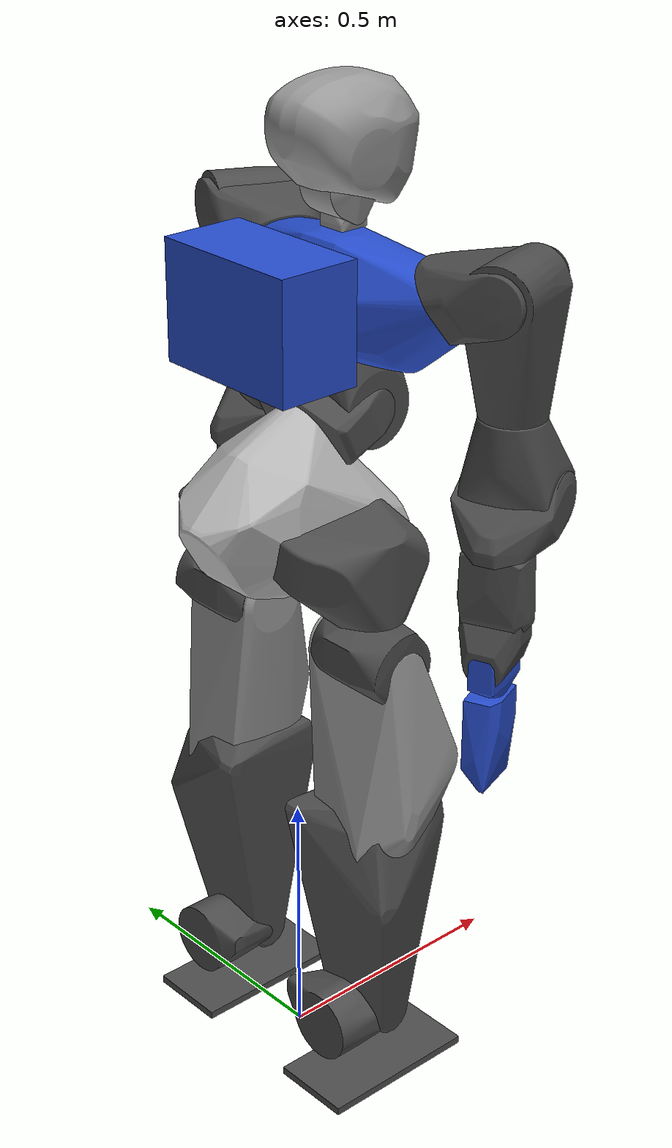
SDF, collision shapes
<sdf version='1.6'>
  <model name='bigman'>
    <link name='base_link'>
      <pose frame=''>0 0 0 0 -0 0</pose>
      <inertial>
        <pose frame=''>-0.022712 -0.000738 0.030477 0 -0 0</pose>
        <mass>11.0661</mass>
        <inertia>
          <ixx>0.0962276</ixx>
          <ixy>0.000139979</ixy>
          <ixz>0.00309245</ixz>
          <iyy>0.0986021</iyy>
          <iyz>0.000138943</iyz>
          <izz>0.0866149</izz>
        </inertia>
      </inertial>
      <collision name='base_link_fixed_joint_lump__Waist_collision'>
        <pose frame=''>0 0 0 0 -0 0</pose>
        <geometry>
          <mesh>
            <scale>0.001 0.001 0.001</scale>
            <uri>model://bigman_urdf/meshes/simple/Waist.STL</uri>
          </mesh>
        </geometry>
      </collision>
      <visual name='base_link_fixed_joint_lump__Waist_visual'>
        <pose frame=''>0 0 0 0 -0 0</pose>
        <geometry>
          <mesh>
            <scale>0.001 0.001 0.001</scale>
            <uri>model://bigman_urdf/meshes/Waist.STL</uri>
          </mesh>
        </geometry>
      </visual>
      <visual name='base_link_fixed_joint_lump__imu_link_visual_1'>
        <pose frame=''>0.0535 0 0.0601 0 -0 0</pose>
        <geometry>
          <box>
            <size>0.01 0.01 0.01</size>
          </box>
        </geometry>
        <material>
          <script>
            <uri>__default__</uri>
            <name>__default__</name>
          </script>
        </material>
      </visual>
      <visual name='base_link_fixed_joint_lump__imu_link2_visual_2'>
        <pose frame=''>0.0135 0 0.0601 0 -0 0</pose>
        <geometry>
          <box>
            <size>0.01 0.01 0.01</size>
          </box>
        </geometry>
        <material>
          <script>
            <uri>__default__</uri>
            <name>__default__</name>
          </script>
        </material>
      </visual>
      <velocity_decay/>
      <velocity_decay/>
      <sensor name='imu_link' type='imu'>
        <always_on>1</always_on>
        <update_rate>1000</update_rate>
        <visualize>1</visualize>
        <topic>__default_topic__</topic>
        <imu>
          <angular_velocity/>
          <linear_acceleration/>
        </imu>
        <pose frame=''>0.0535 0 0.0601 0 -0 0</pose>
      </sensor>
      <gravity>1</gravity>
      <velocity_decay/>
      <sensor name='imu_link2' type='imu'>
        <always_on>1</always_on>
        <update_rate>1000</update_rate>
        <visualize>1</visualize>
        <topic>__default_topic__</topic>
        <imu>
          <angular_velocity/>
          <linear_acceleration/>
        </imu>
        <pose frame=''>0.0135 0 0.0601 0 -0 0</pose>
      </sensor>
    </link>
    <link name='LHipMot'>
      <pose frame=''>0.1059 0.06 0 0 -0 0</pose>
      <inertial>
        <pose frame=''>-0.103482 0.109198 -0.064924 0 -0 0</pose>
        <mass>3.79582</mass>
        <inertia>
          <ixx>0.015639</ixx>
          <ixy>-0.00185047</ixy>
          <ixz>0.00239078</ixz>
          <iyy>0.0235197</iyy>
          <iyz>0.00233032</iyz>
          <izz>0.0209536</izz>
        </inertia>
      </inertial>
      <collision name='LHipMot_collision'>
        <pose frame=''>0 0 0 0 -0 0</pose>
        <geometry>
          <mesh>
            <scale>0.001 -0.001 0.001</scale>
            <uri>model://bigman_urdf/meshes/simple/HipRoll.STL</uri>
          </mesh>
        </geometry>
        <surface>
          <contact>
            <ode/>
          </contact>
          <friction>
            <ode/>
          </friction>
        </surface>
      </collision>
      <visual name='LHipMot_visual'>
        <pose frame=''>0 0 0 0 -0 0</pose>
        <geometry>
          <mesh>
            <scale>0.001 -0.001 0.001</scale>
            <uri>model://bigman_urdf/meshes/HipRoll.STL</uri>
          </mesh>
        </geometry>
        <material>
          <script>
            <name>Gazebo/DarkGrey</name>
            <uri>file://media/materials/scripts/gazebo.material</uri>
          </script>
        </material>
      </visual>
      <gravity>1</gravity>
      <velocity_decay/>
    </link>
    <joint name='LHipLat' type='revolute'>
      <child>LHipMot</child>
      <parent>base_link</parent>
      <axis>
        <xyz>1 0 0</xyz>
        <limit>
          <lower>-0.697778</lower>
          <upper>0.87222</upper>
          <effort>400</effort>
          <velocity>6.283</velocity>
        </limit>
        <dynamics>
          <damping>3</damping>
          <friction>0</friction>
          <spring_reference>0</spring_reference>
          <spring_stiffness>0</spring_stiffness>
        </dynamics>
        <use_parent_model_frame>1</use_parent_model_frame>
      </axis>
      <physics>
        <provide_feedback>1</provide_feedback>
        <ode>
          <provide_feedback>1</provide_feedback>
          <implicit_spring_damper>1</implicit_spring_damper>
          <cfm_damping>1</cfm_damping>
          <limit>
            <cfm>0</cfm>
            <erp>0.2</erp>
          </limit>
        </ode>
      </physics>
    </joint>
    <link name='LThighUpLeg'>
      <pose frame=''>0.017 0.181032 -0.217872 0 -0 0</pose>
      <inertial>
        <pose frame=''>-0.005293 0.022562 0.00567 0 -0 0</pose>
        <mass>3.24021</mass>
        <inertia>
          <ixx>0.0101021</ixx>
          <ixy>-0.000108585</ixy>
          <ixz>0.000252914</ixz>
          <iyy>0.0067147</iyy>
          <iyz>-8.34471e-05</iyz>
          <izz>0.0104851</izz>
        </inertia>
      </inertial>
      <collision name='LThighUpLeg_collision'>
        <pose frame=''>0 0 0 0 -0 0</pose>
        <geometry>
          <mesh>
            <scale>0.001 -0.001 0.001</scale>
            <uri>model://bigman_urdf/meshes/simple/HipYaw.STL</uri>
          </mesh>
        </geometry>
        <surface>
          <contact>
            <ode/>
          </contact>
          <friction>
            <ode/>
          </friction>
        </surface>
      </collision>
      <visual name='LThighUpLeg_visual'>
        <pose frame=''>0 0 0 0 -0 0</pose>
        <geometry>
          <mesh>
            <scale>0.001 -0.001 0.001</scale>
            <uri>model://bigman_urdf/meshes/HipYaw.STL</uri>
          </mesh>
        </geometry>
        <material>
          <script>
            <name>Gazebo/DarkGrey</name>
            <uri>file://media/materials/scripts/gazebo.material</uri>
          </script>
        </material>
      </visual>
      <gravity>1</gravity>
      <velocity_decay/>
    </link>
    <joint name='LHipYaw' type='revolute'>
      <child>LThighUpLeg</child>
      <parent>LHipMot</parent>
      <axis>
        <xyz>0 0 1</xyz>
        <limit>
          <lower>-0.872222</lower>
          <upper>1.57</upper>
          <effort>140</effort>
          <velocity>6.283</velocity>
        </limit>
        <dynamics>
          <damping>3</damping>
          <friction>0</friction>
          <spring_reference>0</spring_reference>
          <spring_stiffness>0</spring_stiffness>
        </dynamics>
        <use_parent_model_frame>1</use_parent_model_frame>
      </axis>
      <physics>
        <provide_feedback>1</provide_feedback>
        <ode>
          <provide_feedback>1</provide_feedback>
          <implicit_spring_damper>1</implicit_spring_damper>
          <cfm_damping>1</cfm_damping>
          <limit>
            <cfm>0</cfm>
            <erp>0.2</erp>
          </limit>
        </ode>
      </physics>
    </joint>
    <link name='LThighLowLeg'>
      <pose frame=''>0.017 0.181032 -0.217872 0 -0 0</pose>
      <inertial>
        <pose frame=''>0.037746 0.02854 -0.193101 0 -0 0</pose>
        <mass>5.09507</mass>
        <inertia>
          <ixx>0.0516079</ixx>
          <ixy>-0.00222535</ixy>
          <ixz>0.00245298</ixz>
          <iyy>0.0443492</iyy>
          <iyz>0.00410069</iyz>
          <izz>0.0233745</izz>
        </inertia>
      </inertial>
      <collision name='LThighLowLeg_collision'>
        <pose frame=''>0 0 0 0 -0 0</pose>
        <geometry>
          <mesh>
            <scale>0.001 -0.001 0.001</scale>
            <uri>model://bigman_urdf/meshes/simple/HipPitch.STL</uri>
          </mesh>
        </geometry>
        <surface>
          <contact>
            <ode/>
          </contact>
          <friction>
            <ode/>
          </friction>
        </surface>
      </collision>
      <visual name='LThighLowLeg_visual'>
        <pose frame=''>0 0 0 0 -0 0</pose>
        <geometry>
          <mesh>
            <scale>0.001 -0.001 0.001</scale>
            <uri>model://bigman_urdf/meshes/HipPitch.STL</uri>
          </mesh>
        </geometry>
        <material>
          <script>
            <name>Gazebo/Grey</name>
            <uri>file://media/materials/scripts/gazebo.material</uri>
          </script>
        </material>
      </visual>
      <gravity>1</gravity>
      <velocity_decay/>
    </link>
    <joint name='LHipSag' type='revolute'>
      <child>LThighLowLeg</child>
      <parent>LThighUpLeg</parent>
      <axis>
        <xyz>0 1 0</xyz>
        <limit>
          <lower>-2.09333</lower>
          <upper>1.04667</upper>
          <effort>400</effort>
          <velocity>6.283</velocity>
        </limit>
        <dynamics>
          <damping>3</damping>
          <friction>0</friction>
          <spring_reference>0</spring_reference>
          <spring_stiffness>0</spring_stiffness>
        </dynamics>
        <use_parent_model_frame>1</use_parent_model_frame>
      </axis>
      <physics>
        <provide_feedback>1</provide_feedback>
        <ode>
          <provide_feedback>1</provide_feedback>
          <implicit_spring_damper>1</implicit_spring_damper>
          <cfm_damping>1</cfm_damping>
          <limit>
            <cfm>0</cfm>
            <erp>0.2</erp>
          </limit>
        </ode>
      </physics>
    </joint>
    <link name='LLowLeg'>
      <pose frame=''>0.017 0.181032 -0.573872 0 -0 0</pose>
      <inertial>
        <pose frame=''>-0.005083 -0.003773 -0.072605 0 -0 0</pose>
        <mass>5.64953</mass>
        <inertia>
          <ixx>0.105355</ixx>
          <ixy>0.000581992</ixy>
          <ixz>0.00167436</ixz>
          <iyy>0.0978578</iyy>
          <iyz>0.00337702</iyz>
          <izz>0.0208541</izz>
        </inertia>
      </inertial>
      <collision name='LLowLeg_collision'>
        <pose frame=''>0 0 0 0 -0 0</pose>
        <geometry>
          <mesh>
            <scale>0.001 -0.001 0.001</scale>
            <uri>model://bigman_urdf/meshes/simple/KneePitchCalf.STL</uri>
          </mesh>
        </geometry>
        <surface>
          <contact>
            <ode>
              <kp>1e+06</kp>
              <kd>100</kd>
              <max_vel>1</max_vel>
              <min_depth>0</min_depth>
            </ode>
          </contact>
          <friction>
            <ode>
              <mu>0.3</mu>
              <mu2>0.3</mu2>
              <fdir1>1 0 0</fdir1>
            </ode>
          </friction>
        </surface>
      </collision>
      <visual name='LLowLeg_visual'>
        <pose frame=''>0 0 0 0 -0 0</pose>
        <geometry>
          <mesh>
            <scale>0.001 -0.001 0.001</scale>
            <uri>model://bigman_urdf/meshes/KneePitchCalf.STL</uri>
          </mesh>
        </geometry>
        <material>
          <script>
            <name>Gazebo/DarkGrey</name>
            <uri>file://media/materials/scripts/gazebo.material</uri>
          </script>
        </material>
      </visual>
      <velocity_decay/>
      <gravity>1</gravity>
      <velocity_decay/>
    </link>
    <joint name='LKneeSag' type='revolute'>
      <child>LLowLeg</child>
      <parent>LThighLowLeg</parent>
      <axis>
        <xyz>0 1 0</xyz>
        <limit>
          <lower>0</lower>
          <upper>2.44222</upper>
          <effort>400</effort>
          <velocity>6.283</velocity>
        </limit>
        <dynamics>
          <damping>3</damping>
          <friction>0</friction>
          <spring_reference>0</spring_reference>
          <spring_stiffness>0</spring_stiffness>
        </dynamics>
        <use_parent_model_frame>1</use_parent_model_frame>
      </axis>
      <physics>
        <provide_feedback>1</provide_feedback>
        <ode>
          <provide_feedback>1</provide_feedback>
          <implicit_spring_damper>1</implicit_spring_damper>
          <cfm_damping>1</cfm_damping>
          <limit>
            <cfm>0</cfm>
            <erp>0.2</erp>
          </limit>
        </ode>
      </physics>
    </joint>
    <link name='LFootmot'>
      <pose frame=''>0.017 0.181032 -0.973872 0 -0 0</pose>
      <inertial>
        <pose frame=''>-0.022024 -0.002568 0.000946 0 -0 0</pose>
        <mass>3.28442</mass>
        <inertia>
          <ixx>0.00755507</ixx>
          <ixy>-0.000674883</ixy>
          <ixz>5.83329e-05</ixz>
          <iyy>0.0112412</iyy>
          <iyz>0.000145521</iyz>
          <izz>0.0133919</izz>
        </inertia>
      </inertial>
      <collision name='LFootmot_collision'>
        <pose frame=''>0 0 0 0 -0 0</pose>
        <geometry>
          <mesh>
            <scale>0.001 -0.001 0.001</scale>
            <uri>model://bigman_urdf/meshes/simple/AnklePitch.STL</uri>
          </mesh>
        </geometry>
        <surface>
          <contact>
            <ode/>
          </contact>
          <friction>
            <ode/>
          </friction>
        </surface>
      </collision>
      <visual name='LFootmot_visual'>
        <pose frame=''>0 0 0 0 -0 0</pose>
        <geometry>
          <mesh>
            <scale>0.001 -0.001 0.001</scale>
            <uri>model://bigman_urdf/meshes/AnklePitch.STL</uri>
          </mesh>
        </geometry>
        <material>
          <script>
            <name>Gazebo/DarkGrey</name>
            <uri>file://media/materials/scripts/gazebo.material</uri>
          </script>
        </material>
      </visual>
      <gravity>1</gravity>
      <velocity_decay/>
    </link>
    <joint name='LAnkSag' type='revolute'>
      <child>LFootmot</child>
      <parent>LLowLeg</parent>
      <axis>
        <xyz>0 1 0</xyz>
        <limit>
          <lower>-1.39556</lower>
          <upper>0.697778</upper>
          <effort>330</effort>
          <velocity>6.283</velocity>
        </limit>
        <dynamics>
          <damping>3</damping>
          <friction>0</friction>
          <spring_reference>0</spring_reference>
          <spring_stiffness>0</spring_stiffness>
        </dynamics>
        <use_parent_model_frame>1</use_parent_model_frame>
      </axis>
      <physics>
        <provide_feedback>1</provide_feedback>
        <ode>
          <provide_feedback>1</provide_feedback>
          <implicit_spring_damper>1</implicit_spring_damper>
          <cfm_damping>1</cfm_damping>
          <limit>
            <cfm>0</cfm>
            <erp>0.2</erp>
          </limit>
        </ode>
      </physics>
    </joint>
    <link name='LFoot'>
      <pose frame=''>0.017 0.181032 -0.973872 0 -0 0</pose>
      <inertial>
        <pose frame=''>-0.006536 0.004794 -0.101804 0 -0 0</pose>
        <mass>3.42638</mass>
        <inertia>
          <ixx>0.0103289</ixx>
          <ixy>0.00016407</ixy>
          <ixz>-0.00201294</ixz>
          <iyy>0.0285402</iyy>
          <iyz>-0.00046315</iyz>
          <izz>0.027995</izz>
        </inertia>
      </inertial>
      <collision name='LFoot_collision'>
        <pose frame=''>0.005 0.01 -0.1359 0 -0 0</pose>
        <geometry>
          <box>
            <size>0.32 0.16 0.015</size>
          </box>
        </geometry>
        <surface>
          <contact>
            <ode>
              <kp>1e+06</kp>
              <kd>100</kd>
              <max_vel>1</max_vel>
              <min_depth>0</min_depth>
            </ode>
          </contact>
          <friction>
            <ode>
              <mu>1</mu>
              <mu2>1</mu2>
              <fdir1>1 0 0</fdir1>
            </ode>
          </friction>
        </surface>
      </collision>
      <visual name='LFoot_visual'>
        <pose frame=''>0 0 0 0 -0 0</pose>
        <geometry>
          <mesh>
            <scale>0.001 -0.001 0.001</scale>
            <uri>model://bigman_urdf/meshes/NewFoot.STL</uri>
          </mesh>
        </geometry>
        <material>
          <script>
            <name>Gazebo/DarkGrey</name>
            <uri>file://media/materials/scripts/gazebo.material</uri>
          </script>
        </material>
      </visual>
      <velocity_decay/>
      <gravity>1</gravity>
      <velocity_decay/>
    </link>
    <joint name='LAnkLat' type='revolute'>
      <child>LFoot</child>
      <parent>LFootmot</parent>
      <axis>
        <xyz>1 0 0</xyz>
        <limit>
          <lower>-0.785</lower>
          <upper>0.785</upper>
          <effort>210</effort>
          <velocity>6.283</velocity>
        </limit>
        <dynamics>
          <damping>3</damping>
          <friction>0</friction>
          <spring_reference>0</spring_reference>
          <spring_stiffness>0</spring_stiffness>
        </dynamics>
        <use_parent_model_frame>1</use_parent_model_frame>
      </axis>
      <physics>
        <ode>
          <limit>
            <cfm>0</cfm>
            <erp>0.2</erp>
          </limit>
          <provide_feedback>1</provide_feedback>
          <implicit_spring_damper>1</implicit_spring_damper>
          <cfm_damping>1</cfm_damping>
        </ode>
        <provide_feedback>1</provide_feedback>
      </physics>
      <sensor name='l_leg_ft' type='force_torque'>
        <force_torque>
          <frame>sensor</frame>
          <measure_direction>child_to_parent</measure_direction>
        </force_torque>
        <always_on>1</always_on>
        <visualize>1</visualize>
        <update_rate>1000</update_rate>
        <pose frame=''>0.005 0 -0.107 0 -0 0</pose>
      </sensor>
    </joint>
    <link name='RHipMot'>
      <pose frame=''>0.1059 -0.06 0 0 -0 0</pose>
      <inertial>
        <pose frame=''>-0.103482 -0.109198 -0.064924 0 -0 0</pose>
        <mass>3.79582</mass>
        <inertia>
          <ixx>0.015639</ixx>
          <ixy>0.00185047</ixy>
          <ixz>0.00239078</ixz>
          <iyy>0.0235197</iyy>
          <iyz>-0.00233032</iyz>
          <izz>0.0209536</izz>
        </inertia>
      </inertial>
      <collision name='RHipMot_collision'>
        <pose frame=''>0 0 0 0 -0 0</pose>
        <geometry>
          <mesh>
            <scale>0.001 0.001 0.001</scale>
            <uri>model://bigman_urdf/meshes/simple/HipRoll.STL</uri>
          </mesh>
        </geometry>
        <surface>
          <contact>
            <ode/>
          </contact>
          <friction>
            <ode/>
          </friction>
        </surface>
      </collision>
      <visual name='RHipMot_visual'>
        <pose frame=''>0 0 0 0 -0 0</pose>
        <geometry>
          <mesh>
            <scale>0.001 0.001 0.001</scale>
            <uri>model://bigman_urdf/meshes/HipRoll.STL</uri>
          </mesh>
        </geometry>
        <material>
          <script>
            <name>Gazebo/DarkGrey</name>
            <uri>file://media/materials/scripts/gazebo.material</uri>
          </script>
        </material>
      </visual>
      <gravity>1</gravity>
      <velocity_decay/>
    </link>
    <joint name='RHipLat' type='revolute'>
      <child>RHipMot</child>
      <parent>base_link</parent>
      <axis>
        <xyz>1 0 0</xyz>
        <limit>
          <lower>-0.87222</lower>
          <upper>0.697778</upper>
          <effort>400</effort>
          <velocity>6.283</velocity>
        </limit>
        <dynamics>
          <damping>3</damping>
          <friction>0</friction>
          <spring_reference>0</spring_reference>
          <spring_stiffness>0</spring_stiffness>
        </dynamics>
        <use_parent_model_frame>1</use_parent_model_frame>
      </axis>
      <physics>
        <provide_feedback>1</provide_feedback>
        <ode>
          <provide_feedback>1</provide_feedback>
          <implicit_spring_damper>1</implicit_spring_damper>
          <cfm_damping>1</cfm_damping>
          <limit>
            <cfm>0</cfm>
            <erp>0.2</erp>
          </limit>
        </ode>
      </physics>
    </joint>
    <link name='RThighUpLeg'>
      <pose frame=''>0.017 -0.181032 -0.217872 0 -0 0</pose>
      <inertial>
        <pose frame=''>-0.005293 -0.022562 0.00567 0 -0 0</pose>
        <mass>3.24021</mass>
        <inertia>
          <ixx>0.0101021</ixx>
          <ixy>0.000108585</ixy>
          <ixz>0.000252914</ixz>
          <iyy>0.0067147</iyy>
          <iyz>8.34471e-05</iyz>
          <izz>0.0104851</izz>
        </inertia>
      </inertial>
      <collision name='RThighUpLeg_collision'>
        <pose frame=''>0 0 0 0 -0 0</pose>
        <geometry>
          <mesh>
            <scale>0.001 0.001 0.001</scale>
            <uri>model://bigman_urdf/meshes/simple/HipYaw.STL</uri>
          </mesh>
        </geometry>
        <surface>
          <contact>
            <ode/>
          </contact>
          <friction>
            <ode/>
          </friction>
        </surface>
      </collision>
      <visual name='RThighUpLeg_visual'>
        <pose frame=''>0 0 0 0 -0 0</pose>
        <geometry>
          <mesh>
            <scale>0.001 0.001 0.001</scale>
            <uri>model://bigman_urdf/meshes/HipYaw.STL</uri>
          </mesh>
        </geometry>
        <material>
          <script>
            <name>Gazebo/DarkGrey</name>
            <uri>file://media/materials/scripts/gazebo.material</uri>
          </script>
        </material>
      </visual>
      <gravity>1</gravity>
      <velocity_decay/>
    </link>
    <joint name='RHipYaw' type='revolute'>
      <child>RThighUpLeg</child>
      <parent>RHipMot</parent>
      <axis>
        <xyz>0 0 1</xyz>
        <limit>
          <lower>-1.57</lower>
          <upper>0.872222</upper>
          <effort>140</effort>
          <velocity>6.283</velocity>
        </limit>
        <dynamics>
          <damping>3</damping>
          <friction>0</friction>
          <spring_reference>0</spring_reference>
          <spring_stiffness>0</spring_stiffness>
        </dynamics>
        <use_parent_model_frame>1</use_parent_model_frame>
      </axis>
      <physics>
        <provide_feedback>1</provide_feedback>
        <ode>
          <provide_feedback>1</provide_feedback>
          <implicit_spring_damper>1</implicit_spring_damper>
          <cfm_damping>1</cfm_damping>
          <limit>
            <cfm>0</cfm>
            <erp>0.2</erp>
          </limit>
        </ode>
      </physics>
    </joint>
    <link name='RThighLowLeg'>
      <pose frame=''>0.017 -0.181032 -0.217872 0 -0 0</pose>
      <inertial>
        <pose frame=''>0.037746 -0.02854 -0.193101 0 -0 0</pose>
        <mass>5.09507</mass>
        <inertia>
          <ixx>0.0516079</ixx>
          <ixy>0.00222535</ixy>
          <ixz>0.00245298</ixz>
          <iyy>0.0443492</iyy>
          <iyz>-0.00410069</iyz>
          <izz>0.0233745</izz>
        </inertia>
      </inertial>
      <collision name='RThighLowLeg_collision'>
        <pose frame=''>0 0 0 0 -0 0</pose>
        <geometry>
          <mesh>
            <scale>0.001 0.001 0.001</scale>
            <uri>model://bigman_urdf/meshes/simple/HipPitch.STL</uri>
          </mesh>
        </geometry>
        <surface>
          <contact>
            <ode/>
          </contact>
          <friction>
            <ode/>
          </friction>
        </surface>
      </collision>
      <visual name='RThighLowLeg_visual'>
        <pose frame=''>0 0 0 0 -0 0</pose>
        <geometry>
          <mesh>
            <scale>0.001 0.001 0.001</scale>
            <uri>model://bigman_urdf/meshes/HipPitch.STL</uri>
          </mesh>
        </geometry>
        <material>
          <script>
            <name>Gazebo/Grey</name>
            <uri>file://media/materials/scripts/gazebo.material</uri>
          </script>
        </material>
      </visual>
      <gravity>1</gravity>
      <velocity_decay/>
    </link>
    <joint name='RHipSag' type='revolute'>
      <child>RThighLowLeg</child>
      <parent>RThighUpLeg</parent>
      <axis>
        <xyz>0 1 0</xyz>
        <limit>
          <lower>-2.09333</lower>
          <upper>1.04667</upper>
          <effort>400</effort>
          <velocity>6.283</velocity>
        </limit>
        <dynamics>
          <damping>3</damping>
          <friction>0</friction>
          <spring_reference>0</spring_reference>
          <spring_stiffness>0</spring_stiffness>
        </dynamics>
        <use_parent_model_frame>1</use_parent_model_frame>
      </axis>
      <physics>
        <provide_feedback>1</provide_feedback>
        <ode>
          <provide_feedback>1</provide_feedback>
          <implicit_spring_damper>1</implicit_spring_damper>
          <cfm_damping>1</cfm_damping>
          <limit>
            <cfm>0</cfm>
            <erp>0.2</erp>
          </limit>
        </ode>
      </physics>
    </joint>
    <link name='RLowLeg'>
      <pose frame=''>0.017 -0.181032 -0.573872 0 -0 0</pose>
      <inertial>
        <pose frame=''>-0.005083 0.003773 -0.072605 0 -0 0</pose>
        <mass>5.64953</mass>
        <inertia>
          <ixx>0.105355</ixx>
          <ixy>-0.000581992</ixy>
          <ixz>0.00167436</ixz>
          <iyy>0.0978578</iyy>
          <iyz>-0.00337702</iyz>
          <izz>0.0208541</izz>
        </inertia>
      </inertial>
      <collision name='RLowLeg_collision'>
        <pose frame=''>0 0 0 0 -0 0</pose>
        <geometry>
          <mesh>
            <scale>0.001 0.001 0.001</scale>
            <uri>model://bigman_urdf/meshes/simple/KneePitchCalf.STL</uri>
          </mesh>
        </geometry>
        <surface>
          <contact>
            <ode>
              <kp>1e+06</kp>
              <kd>100</kd>
              <max_vel>1</max_vel>
              <min_depth>0</min_depth>
            </ode>
          </contact>
          <friction>
            <ode>
              <mu>0.3</mu>
              <mu2>0.3</mu2>
              <fdir1>1 0 0</fdir1>
            </ode>
          </friction>
        </surface>
      </collision>
      <visual name='RLowLeg_visual'>
        <pose frame=''>0 0 0 0 -0 0</pose>
        <geometry>
          <mesh>
            <scale>0.001 0.001 0.001</scale>
            <uri>model://bigman_urdf/meshes/KneePitchCalf.STL</uri>
          </mesh>
        </geometry>
        <material>
          <script>
            <name>Gazebo/DarkGrey</name>
            <uri>file://media/materials/scripts/gazebo.material</uri>
          </script>
        </material>
      </visual>
      <velocity_decay/>
      <gravity>1</gravity>
      <velocity_decay/>
    </link>
    <joint name='RKneeSag' type='revolute'>
      <child>RLowLeg</child>
      <parent>RThighLowLeg</parent>
      <axis>
        <xyz>0 1 0</xyz>
        <limit>
          <lower>0</lower>
          <upper>2.44222</upper>
          <effort>400</effort>
          <velocity>6.283</velocity>
        </limit>
        <dynamics>
          <damping>3</damping>
          <friction>0</friction>
          <spring_reference>0</spring_reference>
          <spring_stiffness>0</spring_stiffness>
        </dynamics>
        <use_parent_model_frame>1</use_parent_model_frame>
      </axis>
      <physics>
        <provide_feedback>1</provide_feedback>
        <ode>
          <provide_feedback>1</provide_feedback>
          <implicit_spring_damper>1</implicit_spring_damper>
          <cfm_damping>1</cfm_damping>
          <limit>
            <cfm>0</cfm>
            <erp>0.2</erp>
          </limit>
        </ode>
      </physics>
    </joint>
    <link name='RFootmot'>
      <pose frame=''>0.017 -0.181032 -0.973872 0 -0 0</pose>
      <inertial>
        <pose frame=''>-0.022024 0.002568 0.000946 0 -0 0</pose>
        <mass>3.28442</mass>
        <inertia>
          <ixx>0.00755507</ixx>
          <ixy>0.000674883</ixy>
          <ixz>5.83329e-05</ixz>
          <iyy>0.0112412</iyy>
          <iyz>-0.000145521</iyz>
          <izz>0.0133919</izz>
        </inertia>
      </inertial>
      <collision name='RFootmot_collision'>
        <pose frame=''>0 0 0 0 -0 0</pose>
        <geometry>
          <mesh>
            <scale>0.001 0.001 0.001</scale>
            <uri>model://bigman_urdf/meshes/simple/AnklePitch.STL</uri>
          </mesh>
        </geometry>
        <surface>
          <contact>
            <ode/>
          </contact>
          <friction>
            <ode/>
          </friction>
        </surface>
      </collision>
      <visual name='RFootmot_visual'>
        <pose frame=''>0 0 0 0 -0 0</pose>
        <geometry>
          <mesh>
            <scale>0.001 0.001 0.001</scale>
            <uri>model://bigman_urdf/meshes/AnklePitch.STL</uri>
          </mesh>
        </geometry>
        <material>
          <script>
            <name>Gazebo/DarkGrey</name>
            <uri>file://media/materials/scripts/gazebo.material</uri>
          </script>
        </material>
      </visual>
      <gravity>1</gravity>
      <velocity_decay/>
    </link>
    <joint name='RAnkSag' type='revolute'>
      <child>RFootmot</child>
      <parent>RLowLeg</parent>
      <axis>
        <xyz>0 1 0</xyz>
        <limit>
          <lower>-1.39556</lower>
          <upper>0.697778</upper>
          <effort>330</effort>
          <velocity>6.283</velocity>
        </limit>
        <dynamics>
          <damping>3</damping>
          <friction>0</friction>
          <spring_reference>0</spring_reference>
          <spring_stiffness>0</spring_stiffness>
        </dynamics>
        <use_parent_model_frame>1</use_parent_model_frame>
      </axis>
      <physics>
        <provide_feedback>1</provide_feedback>
        <ode>
          <provide_feedback>1</provide_feedback>
          <implicit_spring_damper>1</implicit_spring_damper>
          <cfm_damping>1</cfm_damping>
          <limit>
            <cfm>0</cfm>
            <erp>0.2</erp>
          </limit>
        </ode>
      </physics>
    </joint>
    <link name='RFoot'>
      <pose frame=''>0.017 -0.181032 -0.973872 0 -0 0</pose>
      <inertial>
        <pose frame=''>-0.006536 -0.004794 -0.101804 0 -0 0</pose>
        <mass>3.42638</mass>
        <inertia>
          <ixx>0.0103289</ixx>
          <ixy>-0.00016407</ixy>
          <ixz>-0.00201294</ixz>
          <iyy>0.0285402</iyy>
          <iyz>0.00046315</iyz>
          <izz>0.027995</izz>
        </inertia>
      </inertial>
      <collision name='RFoot_collision'>
        <pose frame=''>0.005 -0.01 -0.1359 0 -0 0</pose>
        <geometry>
          <box>
            <size>0.32 0.16 0.015</size>
          </box>
        </geometry>
        <surface>
          <contact>
            <ode>
              <kp>1e+06</kp>
              <kd>100</kd>
              <max_vel>1</max_vel>
              <min_depth>0</min_depth>
            </ode>
          </contact>
          <friction>
            <ode>
              <mu>1</mu>
              <mu2>1</mu2>
              <fdir1>1 0 0</fdir1>
            </ode>
          </friction>
        </surface>
      </collision>
      <visual name='RFoot_visual'>
        <pose frame=''>0 0 0 0 -0 0</pose>
        <geometry>
          <mesh>
            <scale>0.001 0.001 0.001</scale>
            <uri>model://bigman_urdf/meshes/NewFoot.STL</uri>
          </mesh>
        </geometry>
        <material>
          <script>
            <name>Gazebo/DarkGrey</name>
            <uri>file://media/materials/scripts/gazebo.material</uri>
          </script>
        </material>
      </visual>
      <velocity_decay/>
      <gravity>1</gravity>
      <velocity_decay/>
    </link>
    <joint name='RAnkLat' type='revolute'>
      <child>RFoot</child>
      <parent>RFootmot</parent>
      <axis>
        <xyz>1 0 0</xyz>
        <limit>
          <lower>-0.785</lower>
          <upper>0.785</upper>
          <effort>210</effort>
          <velocity>6.283</velocity>
        </limit>
        <dynamics>
          <damping>3</damping>
          <friction>0</friction>
          <spring_reference>0</spring_reference>
          <spring_stiffness>0</spring_stiffness>
        </dynamics>
        <use_parent_model_frame>1</use_parent_model_frame>
      </axis>
      <physics>
        <ode>
          <limit>
            <cfm>0</cfm>
            <erp>0.2</erp>
          </limit>
          <provide_feedback>1</provide_feedback>
          <implicit_spring_damper>1</implicit_spring_damper>
          <cfm_damping>1</cfm_damping>
        </ode>
        <provide_feedback>1</provide_feedback>
      </physics>
      <sensor name='r_leg_ft' type='force_torque'>
        <force_torque>
          <frame>sensor</frame>
          <measure_direction>child_to_parent</measure_direction>
        </force_torque>
        <always_on>1</always_on>
        <visualize>1</visualize>
        <update_rate>1000</update_rate>
        <pose frame=''>0.005 0 -0.107 0 -0 0</pose>
      </sensor>
    </joint>
    <link name='DWL'>
      <pose frame=''>0.1115 0 0.195982 0 -0 0</pose>
      <inertial>
        <pose frame=''>-0.046109 0.022322 -0.022495 0 -0 0</pose>
        <mass>1.44965</mass>
        <inertia>
          <ixx>0.0109676</ixx>
          <ixy>0.00111556</ixy>
          <ixz>0.0003003</ixz>
          <iyy>0.00409572</iyy>
          <iyz>0.00054456</iyz>
          <izz>0.011438</izz>
        </inertia>
      </inertial>
      <collision name='DWL_collision'>
        <pose frame=''>0 0 0 0 -0 0</pose>
        <geometry>
          <mesh>
            <scale>0.001 0.001 0.001</scale>
            <uri>model://bigman_urdf/meshes/simple/TorsoRoll.STL</uri>
          </mesh>
        </geometry>
        <surface>
          <contact>
            <ode/>
          </contact>
          <friction>
            <ode/>
          </friction>
        </surface>
      </collision>
      <visual name='DWL_visual'>
        <pose frame=''>0 0 0 0 -0 0</pose>
        <geometry>
          <mesh>
            <scale>0.001 0.001 0.001</scale>
            <uri>model://bigman_urdf/meshes/TorsoRoll.STL</uri>
          </mesh>
        </geometry>
        <material>
          <script>
            <name>Gazebo/DarkGrey</name>
            <uri>file://media/materials/scripts/gazebo.material</uri>
          </script>
        </material>
      </visual>
      <gravity>1</gravity>
      <velocity_decay/>
    </link>
    <joint name='WaistLat' type='revolute'>
      <child>DWL</child>
      <parent>base_link</parent>
      <axis>
        <xyz>0.8988 0 0.438359</xyz>
        <limit>
          <lower>-0.610865</lower>
          <upper>0.610865</upper>
          <effort>120</effort>
          <velocity>6.283</velocity>
        </limit>
        <dynamics>
          <damping>3</damping>
          <friction>0</friction>
          <spring_reference>0</spring_reference>
          <spring_stiffness>0</spring_stiffness>
        </dynamics>
        <use_parent_model_frame>1</use_parent_model_frame>
      </axis>
      <physics>
        <provide_feedback>1</provide_feedback>
        <ode>
          <provide_feedback>1</provide_feedback>
          <implicit_spring_damper>1</implicit_spring_damper>
          <cfm_damping>1</cfm_damping>
          <limit>
            <cfm>0</cfm>
            <erp>0.2</erp>
          </limit>
        </ode>
      </physics>
    </joint>
    <link name='DWS'>
      <pose frame=''>0.1115 0 0.195982 0 -0 0</pose>
      <inertial>
        <pose frame=''>0.000102 0.009282 0.081136 0 -0 0</pose>
        <mass>5.28826</mass>
        <inertia>
          <ixx>0.0162807</ixx>
          <ixy>-3.23e-06</ixy>
          <ixz>1.424e-05</ixz>
          <iyy>0.0142429</iyy>
          <iyz>0.00075458</iyz>
          <izz>0.00994169</izz>
        </inertia>
      </inertial>
      <collision name='DWS_collision'>
        <pose frame=''>0 0 0 0 -0 0</pose>
        <geometry>
          <mesh>
            <scale>0.001 0.001 0.001</scale>
            <uri>model://bigman_urdf/meshes/simple/TorsoYawPitch.STL</uri>
          </mesh>
        </geometry>
        <surface>
          <contact>
            <ode/>
          </contact>
          <friction>
            <ode/>
          </friction>
        </surface>
      </collision>
      <visual name='DWS_visual'>
        <pose frame=''>0 0 0 0 -0 0</pose>
        <geometry>
          <mesh>
            <scale>0.001 0.001 0.001</scale>
            <uri>model://bigman_urdf/meshes/TorsoYawPitch.STL</uri>
          </mesh>
        </geometry>
        <material>
          <script>
            <name>Gazebo/DarkGrey</name>
            <uri>file://media/materials/scripts/gazebo.material</uri>
          </script>
        </material>
      </visual>
      <gravity>1</gravity>
      <velocity_decay/>
    </link>
    <joint name='WaistSag' type='revolute'>
      <child>DWS</child>
      <parent>DWL</parent>
      <axis>
        <xyz>0 1 0</xyz>
        <limit>
          <lower>-0.349066</lower>
          <upper>1.39626</upper>
          <effort>220</effort>
          <velocity>6.283</velocity>
        </limit>
        <dynamics>
          <damping>3</damping>
          <friction>0</friction>
          <spring_reference>0</spring_reference>
          <spring_stiffness>0</spring_stiffness>
        </dynamics>
        <use_parent_model_frame>1</use_parent_model_frame>
      </axis>
      <physics>
        <provide_feedback>1</provide_feedback>
        <ode>
          <provide_feedback>1</provide_feedback>
          <implicit_spring_damper>1</implicit_spring_damper>
          <cfm_damping>1</cfm_damping>
          <limit>
            <cfm>0</cfm>
            <erp>0.2</erp>
          </limit>
        </ode>
      </physics>
    </joint>
    <link name='DWYTorso'>
      <pose frame=''>0.1115 0 0.418732 0 -0 0</pose>
      <inertial>
        <pose frame=''>-0.051389 0 0.191667 0 -0 0</pose>
        <mass>36</mass>
        <inertia>
          <ixx>1.37388</ixx>
          <ixy>8.16e-05</ixy>
          <ixz>-0.520781</ixz>
          <iyy>1.40124</iyy>
          <iyz>-1.79e-05</iyz>
          <izz>0.532019</izz>
        </inertia>
      </inertial>
      <collision name='DWYTorso_collision'>
        <pose frame=''>0 0 0 0 -0 0</pose>
        <geometry>
          <mesh>
            <scale>0.001 0.001 0.001</scale>
            <uri>model://bigman_urdf/meshes/simple/NewChest.STL</uri>
          </mesh>
        </geometry>
        <surface>
          <contact>
            <ode/>
          </contact>
          <friction>
            <ode/>
          </friction>
        </surface>
      </collision>
      <collision name='DWYTorso_fixed_joint_lump__backpack_collision_1'>
        <pose frame=''>-0.185 0 -0.025 0 -0 0</pose>
        <geometry>
          <box>
            <size>0.16 0.3 0.22</size>
          </box>
        </geometry>
      </collision>
      <visual name='DWYTorso_visual'>
        <pose frame=''>0 0 0 0 -0 0</pose>
        <geometry>
          <mesh>
            <scale>0.001 0.001 0.001</scale>
            <uri>model://bigman_urdf/meshes/NewChest.STL</uri>
          </mesh>
        </geometry>
        <material>
          <script>
            <name>Gazebo/Blue</name>
            <uri>file://media/materials/scripts/gazebo.material</uri>
          </script>
        </material>
      </visual>
      <visual name='DWYTorso_fixed_joint_lump__backpack_visual_1'>
        <pose frame=''>-0.185 0 -0.025 0 -0 0</pose>
        <geometry>
          <box>
            <size>0.16 0.3 0.22</size>
          </box>
        </geometry>
      </visual>
      <gravity>1</gravity>
      <velocity_decay/>
    </link>
    <joint name='WaistYaw' type='revolute'>
      <child>DWYTorso</child>
      <parent>DWS</parent>
      <axis>
        <xyz>0 0 1</xyz>
        <limit>
          <lower>-2.84489</lower>
          <upper>2.84489</upper>
          <effort>120</effort>
          <velocity>6.283</velocity>
        </limit>
        <dynamics>
          <damping>3</damping>
          <friction>0</friction>
          <spring_reference>0</spring_reference>
          <spring_stiffness>0</spring_stiffness>
        </dynamics>
        <use_parent_model_frame>1</use_parent_model_frame>
      </axis>
      <physics>
        <provide_feedback>1</provide_feedback>
        <ode>
          <provide_feedback>1</provide_feedback>
          <implicit_spring_damper>1</implicit_spring_damper>
          <cfm_damping>1</cfm_damping>
          <limit>
            <cfm>0</cfm>
            <erp>0.2</erp>
          </limit>
        </ode>
      </physics>
    </joint>
    <link name='LShp'>
      <pose frame=''>0.157146 0.219164 0.420263 0 0 -0.3491</pose>
      <inertial>
        <pose frame=''>-0.005433 0.0448 0.015811 0 -0 0</pose>
        <mass>1.81746</mass>
        <inertia>
          <ixx>0.00571053</ixx>
          <ixy>-0.00041083</ixy>
          <ixz>-5.13e-05</ixz>
          <iyy>0.0112691</iyy>
          <iyz>3.461e-05</iyz>
          <izz>0.013712</izz>
        </inertia>
      </inertial>
      <collision name='LShp_collision'>
        <pose frame=''>0 0 0 0 -0 0</pose>
        <geometry>
          <mesh>
            <scale>0.001 -0.001 0.001</scale>
            <uri>model://bigman_urdf/meshes/simple/ShoulderPitch.STL</uri>
          </mesh>
        </geometry>
        <surface>
          <contact>
            <ode/>
          </contact>
          <friction>
            <ode/>
          </friction>
        </surface>
      </collision>
      <visual name='LShp_visual'>
        <pose frame=''>0 0 0 0 -0 0</pose>
        <geometry>
          <mesh>
            <scale>0.001 -0.001 0.001</scale>
            <uri>model://bigman_urdf/meshes/ShoulderPitch.STL</uri>
          </mesh>
        </geometry>
        <material>
          <script>
            <name>Gazebo/DarkGrey</name>
            <uri>file://media/materials/scripts/gazebo.material</uri>
          </script>
        </material>
      </visual>
      <gravity>1</gravity>
      <velocity_decay/>
    </link>
    <joint name='LShSag' type='revolute'>
      <child>LShp</child>
      <parent>DWYTorso</parent>
      <axis>
        <xyz>0.254194 0.698319 0.669131</xyz>
        <limit>
          <lower>-2.87979</lower>
          <upper>2.79253</upper>
          <effort>120</effort>
          <velocity>6.283</velocity>
        </limit>
        <dynamics>
          <damping>3</damping>
          <friction>0</friction>
          <spring_reference>0</spring_reference>
          <spring_stiffness>0</spring_stiffness>
        </dynamics>
        <use_parent_model_frame>1</use_parent_model_frame>
      </axis>
      <physics>
        <provide_feedback>1</provide_feedback>
        <ode>
          <provide_feedback>1</provide_feedback>
          <implicit_spring_damper>1</implicit_spring_damper>
          <cfm_damping>1</cfm_damping>
          <limit>
            <cfm>0</cfm>
            <erp>0.2</erp>
          </limit>
        </ode>
      </physics>
    </joint>
    <link name='LShr'>
      <pose frame=''>0.197018 0.328701 0.453903 0 0 -0.3491</pose>
      <inertial>
        <pose frame=''>0.007293 -2.7e-05 -0.075297 0 -0 0</pose>
        <mass>5.00486</mass>
        <inertia>
          <ixx>0.0164434</ixx>
          <ixy>1.187e-05</ixy>
          <ixz>-0.00010546</ixz>
          <iyy>0.018048</iyy>
          <iyz>5.65e-06</iyz>
          <izz>0.0080242</izz>
        </inertia>
      </inertial>
      <collision name='LShr_collision'>
        <pose frame=''>0 0 0 0 -0 0</pose>
        <geometry>
          <mesh>
            <scale>0.001 -0.001 0.001</scale>
            <uri>model://bigman_urdf/meshes/simple/TopUpperArm.STL</uri>
          </mesh>
        </geometry>
        <surface>
          <contact>
            <ode/>
          </contact>
          <friction>
            <ode/>
          </friction>
        </surface>
      </collision>
      <visual name='LShr_visual'>
        <pose frame=''>0 0 0 0 -0 0</pose>
        <geometry>
          <mesh>
            <scale>0.001 -0.001 0.001</scale>
            <uri>model://bigman_urdf/meshes/TopUpperArm.STL</uri>
          </mesh>
        </geometry>
        <material>
          <script>
            <name>Gazebo/DarkGrey</name>
            <uri>file://media/materials/scripts/gazebo.material</uri>
          </script>
        </material>
      </visual>
      <gravity>1</gravity>
      <velocity_decay/>
    </link>
    <joint name='LShLat' type='revolute'>
      <child>LShr</child>
      <parent>LShp</parent>
      <axis>
        <xyz>0.939681 -0.342052 0</xyz>
        <limit>
          <lower>0.0872665</lower>
          <upper>3.85718</upper>
          <effort>120</effort>
          <velocity>6.283</velocity>
        </limit>
        <dynamics>
          <damping>3</damping>
          <friction>0</friction>
          <spring_reference>0</spring_reference>
          <spring_stiffness>0</spring_stiffness>
        </dynamics>
        <use_parent_model_frame>1</use_parent_model_frame>
      </axis>
      <physics>
        <provide_feedback>1</provide_feedback>
        <ode>
          <provide_feedback>1</provide_feedback>
          <implicit_spring_damper>1</implicit_spring_damper>
          <cfm_damping>1</cfm_damping>
          <limit>
            <cfm>0</cfm>
            <erp>0.2</erp>
          </limit>
        </ode>
      </physics>
    </joint>
    <link name='LShy'>
      <pose frame=''>0.197018 0.328701 0.231903 0 0 -0.3491</pose>
      <inertial>
        <pose frame=''>0.027654 0.032586 -0.126988 0 -0 0</pose>
        <mass>3.20289</mass>
        <inertia>
          <ixx>0.0112905</ixx>
          <ixy>-0.00013518</ixy>
          <ixz>-0.0013476</ixz>
          <iyy>0.00984951</iyy>
          <iyz>0.00026836</iyz>
          <izz>0.00728549</izz>
        </inertia>
      </inertial>
      <collision name='LShy_collision'>
        <pose frame=''>0 0 0 0 -0 0</pose>
        <geometry>
          <mesh>
            <scale>0.001 -0.001 0.001</scale>
            <uri>model://bigman_urdf/meshes/simple/BottomUpperArm.STL</uri>
          </mesh>
        </geometry>
        <surface>
          <contact>
            <ode/>
          </contact>
          <friction>
            <ode/>
          </friction>
        </surface>
      </collision>
      <visual name='LShy_visual'>
        <pose frame=''>0 0 0 0 -0 0</pose>
        <geometry>
          <mesh>
            <scale>0.001 -0.001 0.001</scale>
            <uri>model://bigman_urdf/meshes/BottomUpperArm.STL</uri>
          </mesh>
        </geometry>
        <material>
          <script>
            <name>Gazebo/DarkGrey</name>
            <uri>file://media/materials/scripts/gazebo.material</uri>
          </script>
        </material>
      </visual>
      <gravity>1</gravity>
      <velocity_decay/>
    </link>
    <joint name='LShYaw' type='revolute'>
      <child>LShy</child>
      <parent>LShr</parent>
      <axis>
        <xyz>0 0 1</xyz>
        <limit>
          <lower>-2.84489</lower>
          <upper>2.84489</upper>
          <effort>120</effort>
          <velocity>6.283</velocity>
        </limit>
        <dynamics>
          <damping>3</damping>
          <friction>0</friction>
          <spring_reference>0</spring_reference>
          <spring_stiffness>0</spring_stiffness>
        </dynamics>
        <use_parent_model_frame>1</use_parent_model_frame>
      </axis>
      <physics>
        <provide_feedback>1</provide_feedback>
        <ode>
          <provide_feedback>1</provide_feedback>
          <implicit_spring_damper>1</implicit_spring_damper>
          <cfm_damping>1</cfm_damping>
          <limit>
            <cfm>0</cfm>
            <erp>0.2</erp>
          </limit>
        </ode>
      </physics>
    </joint>
    <link name='LElb'>
      <pose frame=''>0.230847 0.316387 0.081903 0 0 -0.3491</pose>
      <inertial>
        <pose frame=''>-0.055755 0.007583 -0.04382 0 -0 0</pose>
        <mass>0.867654</mass>
        <inertia>
          <ixx>0.00403952</ixx>
          <ixy>-0.000349731</ixy>
          <ixz>-0.000684005</ixz>
          <iyy>0.00224606</iyy>
          <iyz>-0.000288444</iyz>
          <izz>0.0044895</izz>
        </inertia>
      </inertial>
      <collision name='LElb_collision'>
        <pose frame=''>0 0 0 0 -0 0</pose>
        <geometry>
          <mesh>
            <scale>0.001 -0.001 0.001</scale>
            <uri>model://bigman_urdf/meshes/simple/Elbow.STL</uri>
          </mesh>
        </geometry>
        <surface>
          <contact>
            <ode/>
          </contact>
          <friction>
            <ode/>
          </friction>
        </surface>
      </collision>
      <visual name='LElb_visual'>
        <pose frame=''>0 0 0 0 -0 0</pose>
        <geometry>
          <mesh>
            <scale>0.001 -0.001 0.001</scale>
            <uri>model://bigman_urdf/meshes/Elbow.STL</uri>
          </mesh>
        </geometry>
        <material>
          <script>
            <name>Gazebo/DarkGrey</name>
            <uri>file://media/materials/scripts/gazebo.material</uri>
          </script>
        </material>
      </visual>
      <gravity>1</gravity>
      <velocity_decay/>
    </link>
    <joint name='LElbj' type='revolute'>
      <child>LElb</child>
      <parent>LShy</parent>
      <axis>
        <xyz>0.342052 0.939681 0</xyz>
        <limit>
          <lower>-2.96706</lower>
          <upper>0.593412</upper>
          <effort>120</effort>
          <velocity>6.283</velocity>
        </limit>
        <dynamics>
          <damping>3</damping>
          <friction>0</friction>
          <spring_reference>0</spring_reference>
          <spring_stiffness>0</spring_stiffness>
        </dynamics>
        <use_parent_model_frame>1</use_parent_model_frame>
      </axis>
      <physics>
        <provide_feedback>1</provide_feedback>
        <ode>
          <provide_feedback>1</provide_feedback>
          <implicit_spring_damper>1</implicit_spring_damper>
          <cfm_damping>1</cfm_damping>
          <limit>
            <cfm>0</cfm>
            <erp>0.2</erp>
          </limit>
        </ode>
      </physics>
    </joint>
    <link name='LForearm'>
      <pose frame=''>0.160371 0.342041 -0.113597 0 0 -0.3491</pose>
      <inertial>
        <pose frame=''>1.3e-05 0.004298 0.044718 0 -0 0</pose>
        <mass>2.21277</mass>
        <inertia>
          <ixx>0.00654284</ixx>
          <ixy>-4.1197e-05</ixy>
          <ixz>3.27273e-06</ixz>
          <iyy>0.00558783</iyy>
          <iyz>0.000420887</iyz>
          <izz>0.0024783</izz>
        </inertia>
      </inertial>
      <collision name='LForearm_collision'>
        <pose frame=''>0 0 0 0 -0 0</pose>
        <geometry>
          <mesh>
            <scale>0.001 -0.001 0.001</scale>
            <uri>model://bigman_urdf/meshes/simple/Forearm.STL</uri>
          </mesh>
        </geometry>
        <surface>
          <contact>
            <ode/>
          </contact>
          <friction>
            <ode/>
          </friction>
        </surface>
      </collision>
      <visual name='LForearm_visual'>
        <pose frame=''>0 0 0 0 -0 0</pose>
        <geometry>
          <mesh>
            <scale>0.001 -0.001 0.001</scale>
            <uri>model://bigman_urdf/meshes/Forearm.STL</uri>
          </mesh>
        </geometry>
        <material>
          <script>
            <name>Gazebo/DarkGrey</name>
            <uri>file://media/materials/scripts/gazebo.material</uri>
          </script>
        </material>
      </visual>
      <gravity>1</gravity>
      <velocity_decay/>
    </link>
    <joint name='LForearmPlate' type='revolute'>
      <child>LForearm</child>
      <parent>LElb</parent>
      <axis>
        <xyz>0 0 1</xyz>
        <limit>
          <lower>-2.529</lower>
          <upper>2.529</upper>
          <effort>60</effort>
          <velocity>6.283</velocity>
        </limit>
        <dynamics>
          <damping>0.03</damping>
          <friction>0</friction>
          <spring_reference>0</spring_reference>
          <spring_stiffness>0</spring_stiffness>
        </dynamics>
        <use_parent_model_frame>1</use_parent_model_frame>
      </axis>
      <physics>
        <provide_feedback>1</provide_feedback>
        <ode>
          <provide_feedback>1</provide_feedback>
          <implicit_spring_damper>1</implicit_spring_damper>
          <cfm_damping>1</cfm_damping>
          <limit>
            <cfm>0</cfm>
            <erp>0.2</erp>
          </limit>
        </ode>
      </physics>
    </joint>
    <link name='LWrMot2'>
      <pose frame=''>0.160371 0.342041 -0.113597 0 0 -0.3491</pose>
      <inertial>
        <pose frame=''>0.009819 0.00138 -0.08038 0 -0 0</pose>
        <mass>1.28381</mass>
        <inertia>
          <ixx>0.00199412</ixx>
          <ixy>2.56971e-05</ixy>
          <ixz>0.000174435</ixz>
          <iyy>0.00217553</iyy>
          <iyz>-0.00012101</iyz>
          <izz>0.00183038</izz>
        </inertia>
      </inertial>
      <collision name='LWrMot2_collision'>
        <pose frame=''>0 0 0 0 -0 0</pose>
        <geometry>
          <mesh>
            <scale>0.001 -0.001 0.001</scale>
            <uri>model://bigman_urdf/meshes/simple/ForearmPitch.STL</uri>
          </mesh>
        </geometry>
        <surface>
          <contact>
            <ode/>
          </contact>
          <friction>
            <ode/>
          </friction>
        </surface>
      </collision>
      <visual name='LWrMot2_visual'>
        <pose frame=''>0 0 0 0 -0 0</pose>
        <geometry>
          <mesh>
            <scale>0.001 -0.001 0.001</scale>
            <uri>model://bigman_urdf/meshes/ForearmPitch.STL</uri>
          </mesh>
        </geometry>
        <material>
          <script>
            <name>Gazebo/DarkGrey</name>
            <uri>file://media/materials/scripts/gazebo.material</uri>
          </script>
        </material>
      </visual>
      <gravity>1</gravity>
      <velocity_decay/>
    </link>
    <joint name='LWrj1' type='revolute'>
      <child>LWrMot2</child>
      <parent>LForearm</parent>
      <axis>
        <xyz>0.342052 0.939681 0</xyz>
        <limit>
          <lower>-1.48</lower>
          <upper>1.48</upper>
          <effort>60</effort>
          <velocity>6.283</velocity>
        </limit>
        <dynamics>
          <damping>0.03</damping>
          <friction>0</friction>
          <spring_reference>0</spring_reference>
          <spring_stiffness>0</spring_stiffness>
        </dynamics>
        <use_parent_model_frame>1</use_parent_model_frame>
      </axis>
      <physics>
        <provide_feedback>1</provide_feedback>
        <ode>
          <provide_feedback>1</provide_feedback>
          <implicit_spring_damper>1</implicit_spring_damper>
          <cfm_damping>1</cfm_damping>
          <limit>
            <cfm>0</cfm>
            <erp>0.2</erp>
          </limit>
        </ode>
      </physics>
    </joint>
    <link name='LWrMot3'>
      <pose frame=''>0.160371 0.342041 -0.205597 0 0 -0.3491</pose>
      <inertial>
        <pose frame=''>0.00185 -3e-06 -0.135735 0 -0 0</pose>
        <mass>1.62801</mass>
        <inertia>
          <ixx>0.00796509</ixx>
          <ixy>7.65758e-08</ixy>
          <ixz>-0.000328563</ixz>
          <iyy>0.00904714</iyy>
          <iyz>3.4951e-07</iyz>
          <izz>0.00199007</izz>
        </inertia>
      </inertial>
      <collision name='LWrMot3_collision'>
        <pose frame=''>0 0 0 0 -0 0</pose>
        <geometry>
          <mesh>
            <scale>0.001 -0.001 0.001</scale>
            <uri>model://bigman_urdf/meshes/simple/ForearmRoll.STL</uri>
          </mesh>
        </geometry>
        <surface>
          <contact>
            <ode/>
          </contact>
          <friction>
            <ode/>
          </friction>
        </surface>
      </collision>
      <collision name='LWrMot3_fixed_joint_lump__LSoftHandLink_collision_1'>
        <pose frame=''>0 0 0 0 -0 0</pose>
        <geometry>
          <mesh>
            <scale>0.001 -0.001 0.001</scale>
            <uri>model://bigman_urdf/meshes/simple/SoftHandOpen.STL</uri>
          </mesh>
        </geometry>
      </collision>
      <visual name='LWrMot3_visual'>
        <pose frame=''>0 0 0 0 -0 0</pose>
        <geometry>
          <mesh>
            <scale>0.001 -0.001 0.001</scale>
            <uri>model://bigman_urdf/meshes/ForearmRoll.STL</uri>
          </mesh>
        </geometry>
        <material>
          <script>
            <name>Gazebo/Blue</name>
            <uri>file://media/materials/scripts/gazebo.material</uri>
          </script>
        </material>
      </visual>
      <visual name='LWrMot3_fixed_joint_lump__LSoftHandLink_visual_1'>
        <pose frame=''>0 0 0 0 -0 0</pose>
        <geometry>
          <mesh>
            <scale>0.001 -0.001 0.001</scale>
            <uri>model://bigman_urdf/meshes/SoftHandOpen.STL</uri>
          </mesh>
        </geometry>
      </visual>
      <velocity_decay/>
      <sensor name='LWrMot3_contact_sensor' type='contact'>
        <contact>
          <collision>LWrMot3_fixed_joint_lump__LSoftHandLink_collision_1</collision>
          <topic>__default_topic__</topic>
        </contact>
      </sensor>
      <velocity_decay/>
      <velocity_decay/>
      <gravity>1</gravity>
      <velocity_decay/>
    </link>
    <joint name='LWrj2' type='revolute'>
      <child>LWrMot3</child>
      <parent>LWrMot2</parent>
      <axis>
        <xyz>0.939681 -0.342052 0</xyz>
        <limit>
          <lower>-1.48</lower>
          <upper>1.48</upper>
          <effort>60</effort>
          <velocity>6.283</velocity>
        </limit>
        <dynamics>
          <damping>0.03</damping>
          <friction>0</friction>
          <spring_reference>0</spring_reference>
          <spring_stiffness>0</spring_stiffness>
        </dynamics>
        <use_parent_model_frame>1</use_parent_model_frame>
      </axis>
      <physics>
        <ode>
          <limit>
            <cfm>0</cfm>
            <erp>0.2</erp>
          </limit>
          <provide_feedback>1</provide_feedback>
          <implicit_spring_damper>1</implicit_spring_damper>
          <cfm_damping>1</cfm_damping>
        </ode>
        <provide_feedback>1</provide_feedback>
      </physics>
      <sensor name='l_arm_ft' type='force_torque'>
        <force_torque>
          <frame>sensor</frame>
          <measure_direction>child_to_parent</measure_direction>
        </force_torque>
        <always_on>1</always_on>
        <visualize>1</visualize>
        <update_rate>1000</update_rate>
        <pose frame=''>0 0 -0.0565 0 -0 0</pose>
      </sensor>
    </joint>
    <link name='NeckYaw'>
      <pose frame=''>0.1115 0 0.418732 0 -0 0</pose>
      <inertial>
        <pose frame=''>0 0 0.1155 0 -0 0</pose>
        <mass>0.35</mass>
        <inertia>
          <ixx>0.000328401</ixx>
          <ixy>0</ixy>
          <ixz>0</ixz>
          <iyy>7.03717e-05</iyy>
          <iyz>0</iyz>
          <izz>0.000328401</izz>
        </inertia>
      </inertial>
      <collision name='NeckYaw_collision'>
        <pose frame=''>0 0 0 0 -0 0</pose>
        <geometry>
          <mesh>
            <scale>0.001 0.001 0.001</scale>
            <uri>model://bigman_urdf/meshes/simple/NeckYaw.STL</uri>
          </mesh>
        </geometry>
        <surface>
          <contact>
            <ode/>
          </contact>
          <friction>
            <ode/>
          </friction>
        </surface>
      </collision>
      <visual name='NeckYaw_visual'>
        <pose frame=''>0 0 0 0 -0 0</pose>
        <geometry>
          <mesh>
            <scale>0.001 0.001 0.001</scale>
            <uri>model://bigman_urdf/meshes/NeckYaw.STL</uri>
          </mesh>
        </geometry>
        <material>
          <script>
            <name>Gazebo/Grey</name>
            <uri>file://media/materials/scripts/gazebo.material</uri>
          </script>
        </material>
      </visual>
      <gravity>1</gravity>
      <velocity_decay/>
    </link>
    <joint name='NeckYawj' type='revolute'>
      <child>NeckYaw</child>
      <parent>DWYTorso</parent>
      <axis>
        <xyz>0 0 1</xyz>
        <limit>
          <lower>-0.610865</lower>
          <upper>0.610865</upper>
          <effort>120</effort>
          <velocity>6.283</velocity>
        </limit>
        <dynamics>
          <damping>3</damping>
          <friction>0</friction>
          <spring_reference>0</spring_reference>
          <spring_stiffness>0</spring_stiffness>
        </dynamics>
        <use_parent_model_frame>1</use_parent_model_frame>
      </axis>
    </joint>
    <link name='NeckPitch'>
      <pose frame=''>0.1115 0 0.535732 0 -0 0</pose>
      <inertial>
        <pose frame=''>-0.022658 2.4e-05 0.145328 0 -0 0</pose>
        <mass>2.04285</mass>
        <inertia>
          <ixx>0.0180071</ixx>
          <ixy>-3.1877e-06</ixy>
          <ixz>0.00767138</ixz>
          <iyy>0.023307</iyy>
          <iyz>1.85732e-06</iyz>
          <izz>0.00971513</izz>
        </inertia>
      </inertial>
      <collision name='NeckPitch_collision'>
        <pose frame=''>0 0 0 0 -0 0</pose>
        <geometry>
          <mesh>
            <scale>0.001 0.001 0.001</scale>
            <uri>model://bigman_urdf/meshes/simple/NeckPitch.STL</uri>
          </mesh>
        </geometry>
        <surface>
          <contact>
            <ode/>
          </contact>
          <friction>
            <ode/>
          </friction>
        </surface>
      </collision>
      <collision name='NeckPitch_fixed_joint_lump__multisense/head_collision_1'>
        <pose frame=''>0.08765 0 0.06475 0 -0 0</pose>
        <geometry>
          <mesh>
            <scale>0.001 0.001 0.001</scale>
            <uri>model://bigman_urdf/meshes/simple/Head.STL</uri>
          </mesh>
        </geometry>
        <surface>
          <contact>
            <ode/>
          </contact>
          <friction>
            <ode>
              <mu>0.9</mu>
              <mu2>0.9</mu2>
            </ode>
          </friction>
        </surface>
      </collision>
      <visual name='NeckPitch_visual'>
        <pose frame=''>0 0 0 0 -0 0</pose>
        <geometry>
          <mesh>
            <scale>0.001 0.001 0.001</scale>
            <uri>model://bigman_urdf/meshes/NeckPitch.STL</uri>
          </mesh>
        </geometry>
        <material>
          <script>
            <name>Gazebo/Grey</name>
            <uri>file://media/materials/scripts/gazebo.material</uri>
          </script>
        </material>
      </visual>
      <visual name='NeckPitch_fixed_joint_lump__multisense/head_visual_1'>
        <pose frame=''>0.08765 0 0.06475 0 -0 0</pose>
        <geometry>
          <mesh>
            <scale>0.001 0.001 0.001</scale>
            <uri>model://bigman_urdf/meshes/Head.STL</uri>
          </mesh>
        </geometry>
        <material>
          <script>
            <uri>__default__</uri>
            <name>__default__</name>
          </script>
        </material>
      </visual>
      <visual name='NeckPitch_fixed_joint_lump__multisense/head_imu_link_visual_2'>
        <pose frame=''>0.04015 0.035 0.06475 0 -0 0</pose>
        <geometry>
          <box>
            <size>0.01 0.01 0.01</size>
          </box>
        </geometry>
        <material>
          <script>
            <uri>__default__</uri>
            <name>__default__</name>
          </script>
        </material>
      </visual>
      <velocity_decay/>
      <velocity_decay/>
      <velocity_decay/>
      <sensor name='head_imu_sensor' type='imu'>
        <always_on>1</always_on>
        <update_rate>1000</update_rate>
        <imu>
          <angular_velocity>
            <x>
              <noise type='gaussian'>
                <mean>0</mean>
                <stddev>0.0002</stddev>
                <bias_mean>7.5e-06</bias_mean>
                <bias_stddev>8e-07</bias_stddev>
              </noise>
            </x>
            <y>
              <noise type='gaussian'>
                <mean>0</mean>
                <stddev>0.0002</stddev>
                <bias_mean>7.5e-06</bias_mean>
                <bias_stddev>8e-07</bias_stddev>
              </noise>
            </y>
            <z>
              <noise type='gaussian'>
                <mean>0</mean>
                <stddev>0.0002</stddev>
                <bias_mean>7.5e-06</bias_mean>
                <bias_stddev>8e-07</bias_stddev>
              </noise>
            </z>
          </angular_velocity>
          <linear_acceleration>
            <x>
              <noise type='gaussian'>
                <mean>0</mean>
                <stddev>0.017</stddev>
                <bias_mean>0.1</bias_mean>
                <bias_stddev>0.001</bias_stddev>
              </noise>
            </x>
            <y>
              <noise type='gaussian'>
                <mean>0</mean>
                <stddev>0.017</stddev>
                <bias_mean>0.1</bias_mean>
                <bias_stddev>0.001</bias_stddev>
              </noise>
            </y>
            <z>
              <noise type='gaussian'>
                <mean>0</mean>
                <stddev>0.017</stddev>
                <bias_mean>0.1</bias_mean>
                <bias_stddev>0.001</bias_stddev>
              </noise>
            </z>
          </linear_acceleration>
        </imu>
        <pose frame=''>0.04015 0.035 0.06475 0 -0 0</pose>
      </sensor>
      <gravity>1</gravity>
      <velocity_decay/>
      <sensor name='stereo_camera' type='multicamera'>
        <update_rate>30</update_rate>
        <camera name='left'>
          <horizontal_fov>1.39626</horizontal_fov>
          <image>
            <width>800</width>
            <height>800</height>
            <format>R8G8B8</format>
          </image>
          <clip>
            <near>0.02</near>
            <far>300</far>
          </clip>
          <noise>
            <type>gaussian</type>
            <mean>0</mean>
            <stddev>0.007</stddev>
          </noise>
        </camera>
        <camera name='right'>
          <pose frame=''>0 -0.07 0 0 -0 0</pose>
          <horizontal_fov>1.39626</horizontal_fov>
          <image>
            <width>800</width>
            <height>800</height>
            <format>R8G8B8</format>
          </image>
          <clip>
            <near>0.02</near>
            <far>300</far>
          </clip>
          <noise>
            <type>gaussian</type>
            <mean>0</mean>
            <stddev>0.007</stddev>
          </noise>
        </camera>
        <plugin name='stereo_camera_controller' filename='libgazebo_ros_multicamera.so'>
          <alwaysOn>true</alwaysOn>
          <updateRate>0.0</updateRate>
          <cameraName>multisense/camera</cameraName>
          <imageTopicName>image_raw</imageTopicName>
          <cameraInfoTopicName>camera_info</cameraInfoTopicName>
          <frameName>multisense/left_camera_optical_frame</frameName>
          <rightFrameName>multisense/right_camera_optical_frame</rightFrameName>
          <hackBaseline>0.07</hackBaseline>
          <distortionK1>0.0</distortionK1>
          <distortionK2>0.0</distortionK2>
          <distortionK3>0.0</distortionK3>
          <distortionT1>0.0</distortionT1>
          <distortionT2>0.0</distortionT2>
        </plugin>
        <pose frame=''>0.08765 0.035 0.06275 0 -0 0</pose>
      </sensor>
    </link>
    <joint name='NeckPitchj' type='revolute'>
      <child>NeckPitch</child>
      <parent>NeckYaw</parent>
      <axis>
        <xyz>0 1 0</xyz>
        <limit>
          <lower>-0.261799</lower>
          <upper>1.0472</upper>
          <effort>120</effort>
          <velocity>6.283</velocity>
        </limit>
        <dynamics>
          <damping>3</damping>
          <friction>0</friction>
          <spring_reference>0</spring_reference>
          <spring_stiffness>0</spring_stiffness>
        </dynamics>
        <use_parent_model_frame>1</use_parent_model_frame>
      </axis>
    </joint>
    <link name='multisense/hokuyo_link'>
      <pose frame=''>0.15455 0 0.688482 0 -0 0</pose>
      <inertial>
        <pose frame=''>0.032428 0.000408 -0.004184 0 -0 0</pose>
        <mass>0.057654</mass>
        <inertia>
          <ixx>3.7174e-05</ixx>
          <ixy>4.9927e-08</ixy>
          <ixz>1.1015e-05</ixz>
          <iyy>4.2412e-05</iyy>
          <iyz>-9.8165e-09</iyz>
          <izz>4.167e-05</izz>
        </inertia>
      </inertial>
      <collision name='multisense/hokuyo_link_collision'>
        <pose frame=''>0.01885 0 -0.02119 0 -0 0</pose>
        <geometry>
          <box>
            <size>0.08 0.06 0.04238</size>
          </box>
        </geometry>
        <surface>
          <contact>
            <ode/>
          </contact>
          <friction>
            <ode>
              <mu>0.9</mu>
              <mu2>0.9</mu2>
            </ode>
          </friction>
        </surface>
      </collision>
      <collision name='multisense/hokuyo_link_collision_1'>
        <pose frame=''>0.03 0 0.0235 0 -0 0</pose>
        <geometry>
          <cylinder>
            <length>0.047</length>
            <radius>0.024425</radius>
          </cylinder>
        </geometry>
        <surface>
          <contact>
            <ode/>
          </contact>
          <friction>
            <ode>
              <mu>0.9</mu>
              <mu2>0.9</mu2>
            </ode>
          </friction>
        </surface>
      </collision>
      <visual name='multisense/hokuyo_link_visual'>
        <pose frame=''>0 0 0 1.5708 -0 1.5708</pose>
        <geometry>
          <mesh>
            <scale>1 1 1</scale>
            <uri>model://bigman_urdf/meshes/hokuyo_link.STL</uri>
          </mesh>
        </geometry>
        <material>
          <script>
            <uri>__default__</uri>
            <name>__default__</name>
          </script>
        </material>
      </visual>
      <velocity_decay/>
      <gravity>1</gravity>
      <velocity_decay/>
      <sensor name='head_hokuyo_sensor' type='ray'>
        <visualize>1</visualize>
        <update_rate>40</update_rate>
        <ray>
          <scan>
            <horizontal>
              <samples>720</samples>
              <resolution>1</resolution>
              <min_angle>-1.5708</min_angle>
              <max_angle>1.5708</max_angle>
            </horizontal>
          </scan>
          <range>
            <min>0.1</min>
            <max>30</max>
            <resolution>0.01</resolution>
          </range>
          <noise>
            <type>gaussian</type>
            <mean>0</mean>
            <stddev>0.01</stddev>
          </noise>
        </ray>
        <plugin name='gazebo_ros_head_hokuyo_controller' filename='libgazebo_ros_laser.so'>
          <topicName>/multisense/lidar_scan</topicName>
          <frameName>multisense/head_hokuyo_frame</frameName>
        </plugin>
        <pose frame=''>0.03 0 0.015 0 -0 0</pose>
      </sensor>
    </link>
    <joint name='hokuyo_joint' type='revolute'>
      <child>multisense/hokuyo_link</child>
      <parent>NeckPitch</parent>
      <axis>
        <xyz>1 0 0</xyz>
        <limit>
          <lower>-1e+16</lower>
          <upper>1e+16</upper>
        </limit>
        <dynamics>
          <damping>0.01</damping>
          <friction>0</friction>
          <spring_reference>0</spring_reference>
          <spring_stiffness>0</spring_stiffness>
        </dynamics>
        <use_parent_model_frame>1</use_parent_model_frame>
      </axis>
      <physics>
        <ode>
          <implicit_spring_damper>1</implicit_spring_damper>
          <cfm_damping>1</cfm_damping>
          <limit>
            <cfm>0</cfm>
            <erp>0.2</erp>
          </limit>
        </ode>
      </physics>
    </joint>
    <link name='RShp'>
      <pose frame=''>0.157146 -0.219164 0.420263 0 -0 0.3491</pose>
      <inertial>
        <pose frame=''>-0.005433 -0.0448 0.015811 0 -0 0</pose>
        <mass>1.81746</mass>
        <inertia>
          <ixx>0.00571053</ixx>
          <ixy>0.00041083</ixy>
          <ixz>-5.13e-05</ixz>
          <iyy>0.0112691</iyy>
          <iyz>-3.461e-05</iyz>
          <izz>0.013712</izz>
        </inertia>
      </inertial>
      <collision name='RShp_collision'>
        <pose frame=''>0 0 0 0 -0 0</pose>
        <geometry>
          <mesh>
            <scale>0.001 0.001 0.001</scale>
            <uri>model://bigman_urdf/meshes/simple/ShoulderPitch.STL</uri>
          </mesh>
        </geometry>
        <surface>
          <contact>
            <ode/>
          </contact>
          <friction>
            <ode/>
          </friction>
        </surface>
      </collision>
      <visual name='RShp_visual'>
        <pose frame=''>0 0 0 0 -0 0</pose>
        <geometry>
          <mesh>
            <scale>0.001 0.001 0.001</scale>
            <uri>model://bigman_urdf/meshes/ShoulderPitch.STL</uri>
          </mesh>
        </geometry>
        <material>
          <script>
            <name>Gazebo/DarkGrey</name>
            <uri>file://media/materials/scripts/gazebo.material</uri>
          </script>
        </material>
      </visual>
      <gravity>1</gravity>
      <velocity_decay/>
    </link>
    <joint name='RShSag' type='revolute'>
      <child>RShp</child>
      <parent>DWYTorso</parent>
      <axis>
        <xyz>-0.254194 0.698319 -0.669131</xyz>
        <limit>
          <lower>-2.84489</lower>
          <upper>2.80998</upper>
          <effort>120</effort>
          <velocity>6.283</velocity>
        </limit>
        <dynamics>
          <damping>3</damping>
          <friction>0</friction>
          <spring_reference>0</spring_reference>
          <spring_stiffness>0</spring_stiffness>
        </dynamics>
        <use_parent_model_frame>1</use_parent_model_frame>
      </axis>
      <physics>
        <provide_feedback>1</provide_feedback>
        <ode>
          <provide_feedback>1</provide_feedback>
          <implicit_spring_damper>1</implicit_spring_damper>
          <cfm_damping>1</cfm_damping>
          <limit>
            <cfm>0</cfm>
            <erp>0.2</erp>
          </limit>
        </ode>
      </physics>
    </joint>
    <link name='RShr'>
      <pose frame=''>0.197018 -0.328701 0.453903 0 -0 0.3491</pose>
      <inertial>
        <pose frame=''>0.007293 2.7e-05 -0.075297 0 -0 0</pose>
        <mass>5.00486</mass>
        <inertia>
          <ixx>0.0164434</ixx>
          <ixy>-1.187e-05</ixy>
          <ixz>-0.00010546</ixz>
          <iyy>0.018048</iyy>
          <iyz>-5.65e-06</iyz>
          <izz>0.0080242</izz>
        </inertia>
      </inertial>
      <collision name='RShr_collision'>
        <pose frame=''>0 0 0 0 -0 0</pose>
        <geometry>
          <mesh>
            <scale>0.001 0.001 0.001</scale>
            <uri>model://bigman_urdf/meshes/simple/TopUpperArm.STL</uri>
          </mesh>
        </geometry>
        <surface>
          <contact>
            <ode/>
          </contact>
          <friction>
            <ode/>
          </friction>
        </surface>
      </collision>
      <visual name='RShr_visual'>
        <pose frame=''>0 0 0 0 -0 0</pose>
        <geometry>
          <mesh>
            <scale>0.001 0.001 0.001</scale>
            <uri>model://bigman_urdf/meshes/TopUpperArm.STL</uri>
          </mesh>
        </geometry>
        <material>
          <script>
            <name>Gazebo/DarkGrey</name>
            <uri>file://media/materials/scripts/gazebo.material</uri>
          </script>
        </material>
      </visual>
      <gravity>1</gravity>
      <velocity_decay/>
    </link>
    <joint name='RShLat' type='revolute'>
      <child>RShr</child>
      <parent>RShp</parent>
      <axis>
        <xyz>0.939681 0.342052 0</xyz>
        <limit>
          <lower>-3.85718</lower>
          <upper>-0.122173</upper>
          <effort>120</effort>
          <velocity>6.283</velocity>
        </limit>
        <dynamics>
          <damping>3</damping>
          <friction>0</friction>
          <spring_reference>0</spring_reference>
          <spring_stiffness>0</spring_stiffness>
        </dynamics>
        <use_parent_model_frame>1</use_parent_model_frame>
      </axis>
      <physics>
        <provide_feedback>1</provide_feedback>
        <ode>
          <provide_feedback>1</provide_feedback>
          <implicit_spring_damper>1</implicit_spring_damper>
          <cfm_damping>1</cfm_damping>
          <limit>
            <cfm>0</cfm>
            <erp>0.2</erp>
          </limit>
        </ode>
      </physics>
    </joint>
    <link name='RShy'>
      <pose frame=''>0.197018 -0.328701 0.231903 0 -0 0.3491</pose>
      <inertial>
        <pose frame=''>0.027654 -0.032586 -0.126988 0 -0 0</pose>
        <mass>3.20289</mass>
        <inertia>
          <ixx>0.0112905</ixx>
          <ixy>0.00013518</ixy>
          <ixz>-0.0013476</ixz>
          <iyy>0.00984951</iyy>
          <iyz>-0.00026836</iyz>
          <izz>0.00728549</izz>
        </inertia>
      </inertial>
      <collision name='RShy_collision'>
        <pose frame=''>0 0 0 0 -0 0</pose>
        <geometry>
          <mesh>
            <scale>0.001 0.001 0.001</scale>
            <uri>model://bigman_urdf/meshes/simple/BottomUpperArm.STL</uri>
          </mesh>
        </geometry>
        <surface>
          <contact>
            <ode/>
          </contact>
          <friction>
            <ode/>
          </friction>
        </surface>
      </collision>
      <visual name='RShy_visual'>
        <pose frame=''>0 0 0 0 -0 0</pose>
        <geometry>
          <mesh>
            <scale>0.001 0.001 0.001</scale>
            <uri>model://bigman_urdf/meshes/BottomUpperArm.STL</uri>
          </mesh>
        </geometry>
        <material>
          <script>
            <name>Gazebo/DarkGrey</name>
            <uri>file://media/materials/scripts/gazebo.material</uri>
          </script>
        </material>
      </visual>
      <gravity>1</gravity>
      <velocity_decay/>
    </link>
    <joint name='RShYaw' type='revolute'>
      <child>RShy</child>
      <parent>RShr</parent>
      <axis>
        <xyz>0 0 1</xyz>
        <limit>
          <lower>-2.86234</lower>
          <upper>2.82743</upper>
          <effort>120</effort>
          <velocity>6.283</velocity>
        </limit>
        <dynamics>
          <damping>3</damping>
          <friction>0</friction>
          <spring_reference>0</spring_reference>
          <spring_stiffness>0</spring_stiffness>
        </dynamics>
        <use_parent_model_frame>1</use_parent_model_frame>
      </axis>
      <physics>
        <provide_feedback>1</provide_feedback>
        <ode>
          <provide_feedback>1</provide_feedback>
          <implicit_spring_damper>1</implicit_spring_damper>
          <cfm_damping>1</cfm_damping>
          <limit>
            <cfm>0</cfm>
            <erp>0.2</erp>
          </limit>
        </ode>
      </physics>
    </joint>
    <link name='RElb'>
      <pose frame=''>0.230847 -0.316387 0.081903 0 -0 0.3491</pose>
      <inertial>
        <pose frame=''>-0.055755 -0.007583 -0.04382 0 -0 0</pose>
        <mass>0.867654</mass>
        <inertia>
          <ixx>0.00403952</ixx>
          <ixy>0.000349731</ixy>
          <ixz>-0.000684005</ixz>
          <iyy>0.00224606</iyy>
          <iyz>0.000288444</iyz>
          <izz>0.0044895</izz>
        </inertia>
      </inertial>
      <collision name='RElb_collision'>
        <pose frame=''>0 0 0 0 -0 0</pose>
        <geometry>
          <mesh>
            <scale>0.001 0.001 0.001</scale>
            <uri>model://bigman_urdf/meshes/simple/Elbow.STL</uri>
          </mesh>
        </geometry>
        <surface>
          <contact>
            <ode/>
          </contact>
          <friction>
            <ode/>
          </friction>
        </surface>
      </collision>
      <visual name='RElb_visual'>
        <pose frame=''>0 0 0 0 -0 0</pose>
        <geometry>
          <mesh>
            <scale>0.001 0.001 0.001</scale>
            <uri>model://bigman_urdf/meshes/Elbow.STL</uri>
          </mesh>
        </geometry>
        <material>
          <script>
            <name>Gazebo/DarkGrey</name>
            <uri>file://media/materials/scripts/gazebo.material</uri>
          </script>
        </material>
      </visual>
      <gravity>1</gravity>
      <velocity_decay/>
    </link>
    <joint name='RElbj' type='revolute'>
      <child>RElb</child>
      <parent>RShy</parent>
      <axis>
        <xyz>-0.342052 0.939681 0</xyz>
        <limit>
          <lower>-2.96706</lower>
          <upper>0.593412</upper>
          <effort>120</effort>
          <velocity>6.283</velocity>
        </limit>
        <dynamics>
          <damping>3</damping>
          <friction>0</friction>
          <spring_reference>0</spring_reference>
          <spring_stiffness>0</spring_stiffness>
        </dynamics>
        <use_parent_model_frame>1</use_parent_model_frame>
      </axis>
      <physics>
        <provide_feedback>1</provide_feedback>
        <ode>
          <provide_feedback>1</provide_feedback>
          <implicit_spring_damper>1</implicit_spring_damper>
          <cfm_damping>1</cfm_damping>
          <limit>
            <cfm>0</cfm>
            <erp>0.2</erp>
          </limit>
        </ode>
      </physics>
    </joint>
    <link name='RForearm'>
      <pose frame=''>0.160371 -0.342041 -0.113597 0 -0 0.3491</pose>
      <inertial>
        <pose frame=''>1.3e-05 -0.004298 0.044718 0 -0 0</pose>
        <mass>2.21277</mass>
        <inertia>
          <ixx>0.00654284</ixx>
          <ixy>4.1197e-05</ixy>
          <ixz>3.27273e-06</ixz>
          <iyy>0.00558783</iyy>
          <iyz>-0.000420887</iyz>
          <izz>0.0024783</izz>
        </inertia>
      </inertial>
      <collision name='RForearm_collision'>
        <pose frame=''>0 0 0 0 -0 0</pose>
        <geometry>
          <mesh>
            <scale>0.001 0.001 0.001</scale>
            <uri>model://bigman_urdf/meshes/simple/Forearm.STL</uri>
          </mesh>
        </geometry>
        <surface>
          <contact>
            <ode/>
          </contact>
          <friction>
            <ode/>
          </friction>
        </surface>
      </collision>
      <visual name='RForearm_visual'>
        <pose frame=''>0 0 0 0 -0 0</pose>
        <geometry>
          <mesh>
            <scale>0.001 0.001 0.001</scale>
            <uri>model://bigman_urdf/meshes/Forearm.STL</uri>
          </mesh>
        </geometry>
        <material>
          <script>
            <name>Gazebo/DarkGrey</name>
            <uri>file://media/materials/scripts/gazebo.material</uri>
          </script>
        </material>
      </visual>
      <gravity>1</gravity>
      <velocity_decay/>
    </link>
    <joint name='RForearmPlate' type='revolute'>
      <child>RForearm</child>
      <parent>RElb</parent>
      <axis>
        <xyz>0 0 1</xyz>
        <limit>
          <lower>-2.529</lower>
          <upper>2.529</upper>
          <effort>60</effort>
          <velocity>6.283</velocity>
        </limit>
        <dynamics>
          <damping>0.03</damping>
          <friction>0</friction>
          <spring_reference>0</spring_reference>
          <spring_stiffness>0</spring_stiffness>
        </dynamics>
        <use_parent_model_frame>1</use_parent_model_frame>
      </axis>
      <physics>
        <provide_feedback>1</provide_feedback>
        <ode>
          <provide_feedback>1</provide_feedback>
          <implicit_spring_damper>1</implicit_spring_damper>
          <cfm_damping>1</cfm_damping>
          <limit>
            <cfm>0</cfm>
            <erp>0.2</erp>
          </limit>
        </ode>
      </physics>
    </joint>
    <link name='RWrMot2'>
      <pose frame=''>0.160371 -0.342041 -0.113597 0 -0 0.3491</pose>
      <inertial>
        <pose frame=''>0.009819 -0.00138 -0.08038 0 -0 0</pose>
        <mass>1.28381</mass>
        <inertia>
          <ixx>0.00199412</ixx>
          <ixy>-2.56971e-05</ixy>
          <ixz>0.000174435</ixz>
          <iyy>0.00217553</iyy>
          <iyz>0.00012101</iyz>
          <izz>0.00183038</izz>
        </inertia>
      </inertial>
      <collision name='RWrMot2_collision'>
        <pose frame=''>0 0 0 0 -0 0</pose>
        <geometry>
          <mesh>
            <scale>0.001 0.001 0.001</scale>
            <uri>model://bigman_urdf/meshes/simple/ForearmPitch.STL</uri>
          </mesh>
        </geometry>
        <surface>
          <contact>
            <ode/>
          </contact>
          <friction>
            <ode/>
          </friction>
        </surface>
      </collision>
      <visual name='RWrMot2_visual'>
        <pose frame=''>0 0 0 0 -0 0</pose>
        <geometry>
          <mesh>
            <scale>0.001 0.001 0.001</scale>
            <uri>model://bigman_urdf/meshes/ForearmPitch.STL</uri>
          </mesh>
        </geometry>
        <material>
          <script>
            <name>Gazebo/DarkGrey</name>
            <uri>file://media/materials/scripts/gazebo.material</uri>
          </script>
        </material>
      </visual>
      <gravity>1</gravity>
      <velocity_decay/>
    </link>
    <joint name='RWrj1' type='revolute'>
      <child>RWrMot2</child>
      <parent>RForearm</parent>
      <axis>
        <xyz>-0.342052 0.939681 0</xyz>
        <limit>
          <lower>-1.48</lower>
          <upper>1.48</upper>
          <effort>60</effort>
          <velocity>6.283</velocity>
        </limit>
        <dynamics>
          <damping>0.03</damping>
          <friction>0</friction>
          <spring_reference>0</spring_reference>
          <spring_stiffness>0</spring_stiffness>
        </dynamics>
        <use_parent_model_frame>1</use_parent_model_frame>
      </axis>
      <physics>
        <provide_feedback>1</provide_feedback>
        <ode>
          <provide_feedback>1</provide_feedback>
          <implicit_spring_damper>1</implicit_spring_damper>
          <cfm_damping>1</cfm_damping>
          <limit>
            <cfm>0</cfm>
            <erp>0.2</erp>
          </limit>
        </ode>
      </physics>
    </joint>
    <link name='RWrMot3'>
      <pose frame=''>0.160371 -0.342041 -0.205597 0 -0 0.3491</pose>
      <inertial>
        <pose frame=''>0.00185 3e-06 -0.135735 0 -0 0</pose>
        <mass>1.62801</mass>
        <inertia>
          <ixx>0.00796509</ixx>
          <ixy>-7.65758e-08</ixy>
          <ixz>-0.000328563</ixz>
          <iyy>0.00904714</iyy>
          <iyz>-3.4951e-07</iyz>
          <izz>0.00199007</izz>
        </inertia>
      </inertial>
      <collision name='RWrMot3_collision'>
        <pose frame=''>0 0 0 0 -0 0</pose>
        <geometry>
          <mesh>
            <scale>0.001 0.001 0.001</scale>
            <uri>model://bigman_urdf/meshes/simple/ForearmRoll.STL</uri>
          </mesh>
        </geometry>
        <surface>
          <contact>
            <ode/>
          </contact>
          <friction>
            <ode/>
          </friction>
        </surface>
      </collision>
      <collision name='RWrMot3_fixed_joint_lump__RSoftHandLink_collision_1'>
        <pose frame=''>0 0 0 0 -0 0</pose>
        <geometry>
          <mesh>
            <scale>0.001 0.001 0.001</scale>
            <uri>model://bigman_urdf/meshes/simple/SoftHandOpen.STL</uri>
          </mesh>
        </geometry>
      </collision>
      <visual name='RWrMot3_visual'>
        <pose frame=''>0 0 0 0 -0 0</pose>
        <geometry>
          <mesh>
            <scale>0.001 0.001 0.001</scale>
            <uri>model://bigman_urdf/meshes/ForearmRoll.STL</uri>
          </mesh>
        </geometry>
        <material>
          <script>
            <name>Gazebo/Blue</name>
            <uri>file://media/materials/scripts/gazebo.material</uri>
          </script>
        </material>
      </visual>
      <visual name='RWrMot3_fixed_joint_lump__RSoftHandLink_visual_1'>
        <pose frame=''>0 0 0 0 -0 0</pose>
        <geometry>
          <mesh>
            <scale>0.001 0.001 0.001</scale>
            <uri>model://bigman_urdf/meshes/SoftHandOpen.STL</uri>
          </mesh>
        </geometry>
      </visual>
      <velocity_decay/>
      <sensor name='RWrMot3_contact_sensor' type='contact'>
        <contact>
          <collision>RWrMot3_fixed_joint_lump__RSoftHandLink_collision_1</collision>
          <topic>__default_topic__</topic>
        </contact>
      </sensor>
      <velocity_decay/>
      <velocity_decay/>
      <gravity>1</gravity>
      <velocity_decay/>
    </link>
    <joint name='RWrj2' type='revolute'>
      <child>RWrMot3</child>
      <parent>RWrMot2</parent>
      <axis>
        <xyz>0.939681 0.342052 0</xyz>
        <limit>
          <lower>-1.48</lower>
          <upper>1.48</upper>
          <effort>60</effort>
          <velocity>6.283</velocity>
        </limit>
        <dynamics>
          <damping>0.03</damping>
          <friction>0</friction>
          <spring_reference>0</spring_reference>
          <spring_stiffness>0</spring_stiffness>
        </dynamics>
        <use_parent_model_frame>1</use_parent_model_frame>
      </axis>
      <physics>
        <ode>
          <limit>
            <cfm>0</cfm>
            <erp>0.2</erp>
          </limit>
          <provide_feedback>1</provide_feedback>
          <implicit_spring_damper>1</implicit_spring_damper>
          <cfm_damping>1</cfm_damping>
        </ode>
        <provide_feedback>1</provide_feedback>
      </physics>
      <sensor name='r_arm_ft' type='force_torque'>
        <force_torque>
          <frame>sensor</frame>
          <measure_direction>child_to_parent</measure_direction>
        </force_torque>
        <always_on>1</always_on>
        <visualize>1</visualize>
        <update_rate>1000</update_rate>
        <pose frame=''>0 0 -0.0565 0 -0 0</pose>
      </sensor>
    </joint>
    <plugin name='multisense_plugin' filename='libMultiSenseSLPlugin2.so'/>
    <plugin name='xbot_plugin_handler' filename='libGazeboXBotPlugin.so'>
      <path_to_config_file>configs/ADVR_shared/bigman/configs/config_walkman_floating_base.yaml</path_to_config_file>
    </plugin>
    <static>0</static>
    <plugin name='magnetic_LSoftHand' filename='libmagnetic.so'>
      <link_name>LWrMot3</link_name>
    </plugin>
    <plugin name='magnetic_RSoftHand' filename='libmagnetic.so'>
      <link_name>RWrMot3</link_name>
    </plugin>
    <pose frame=''>0 0 1.12 0 -0 0</pose>
  </model>
</sdf>
